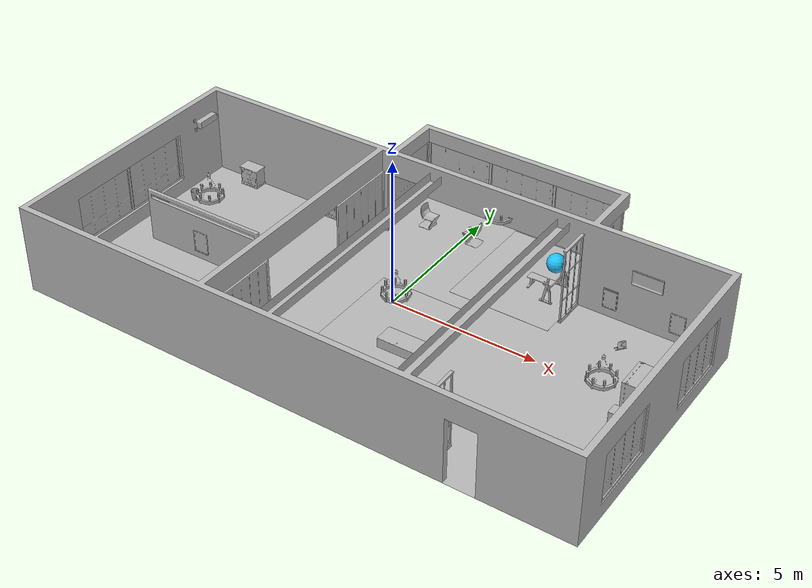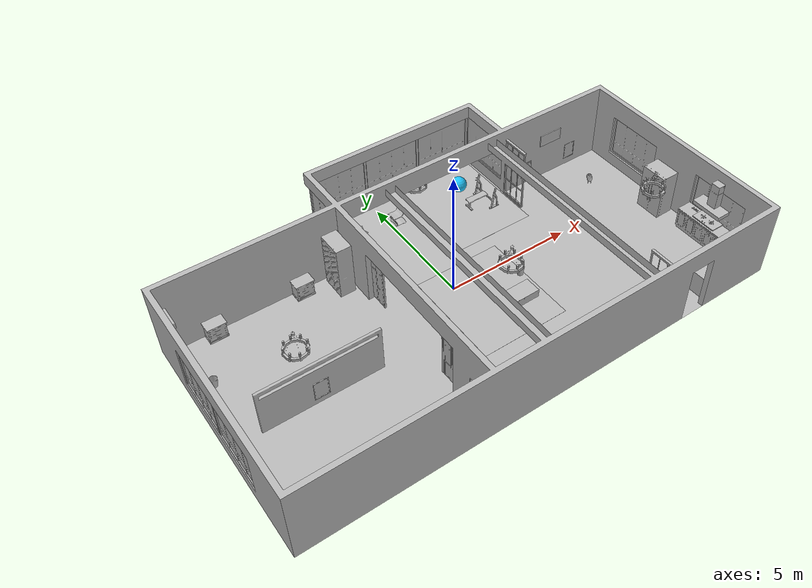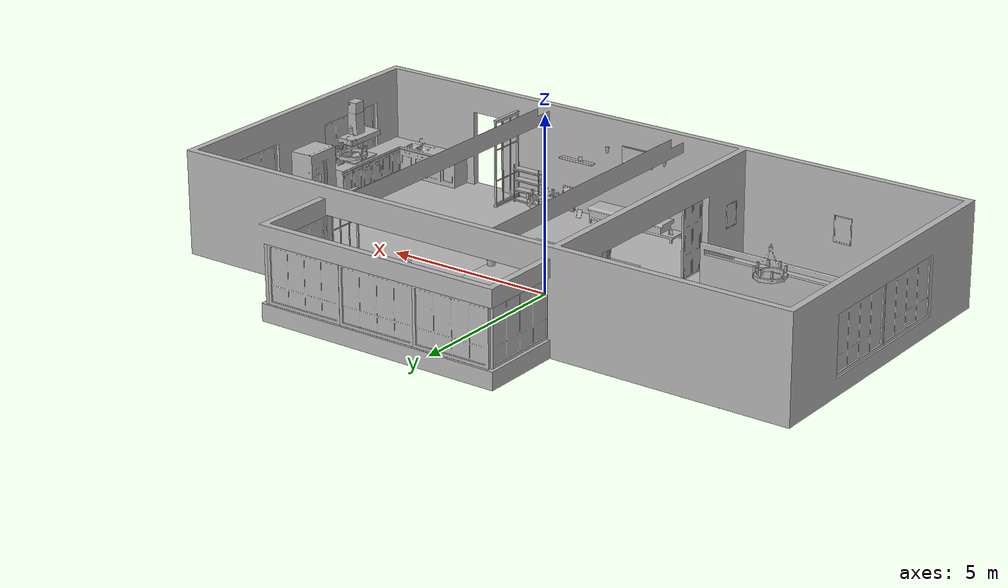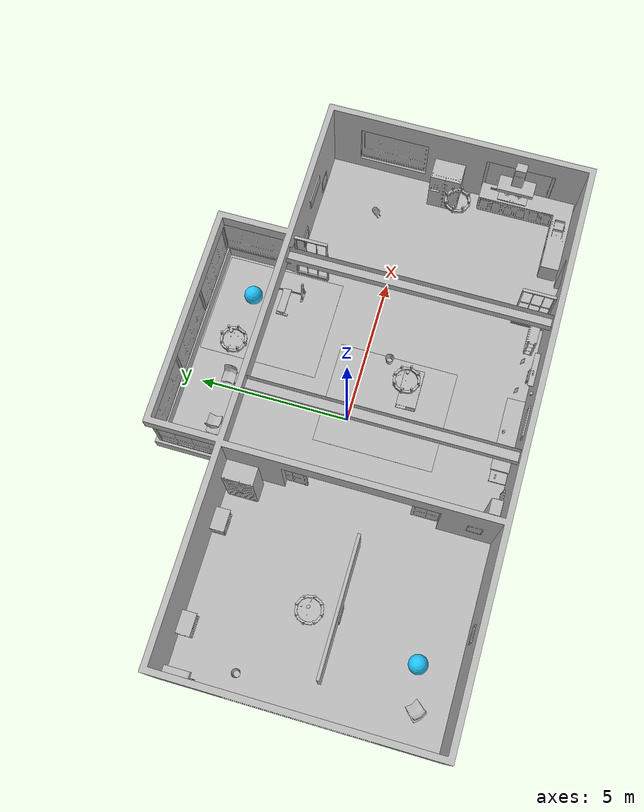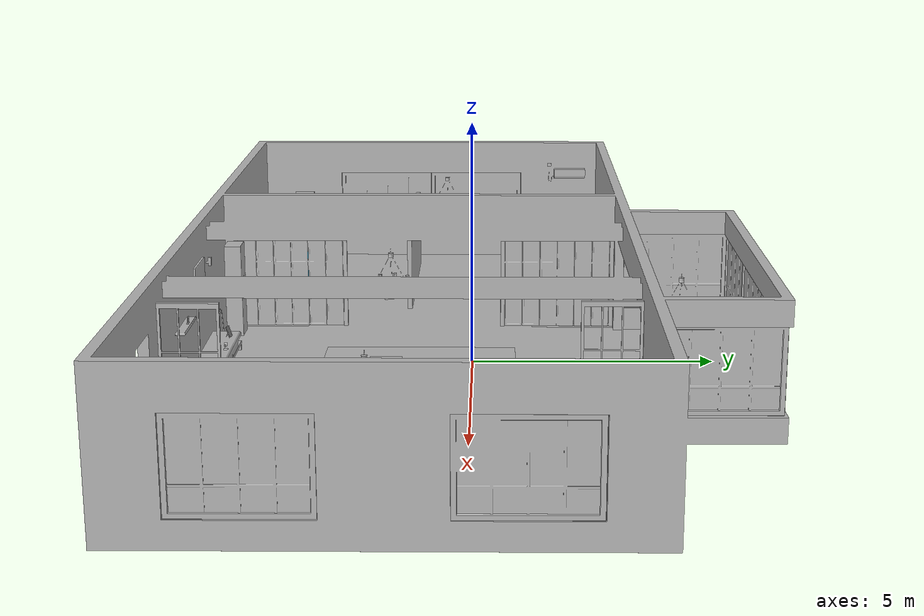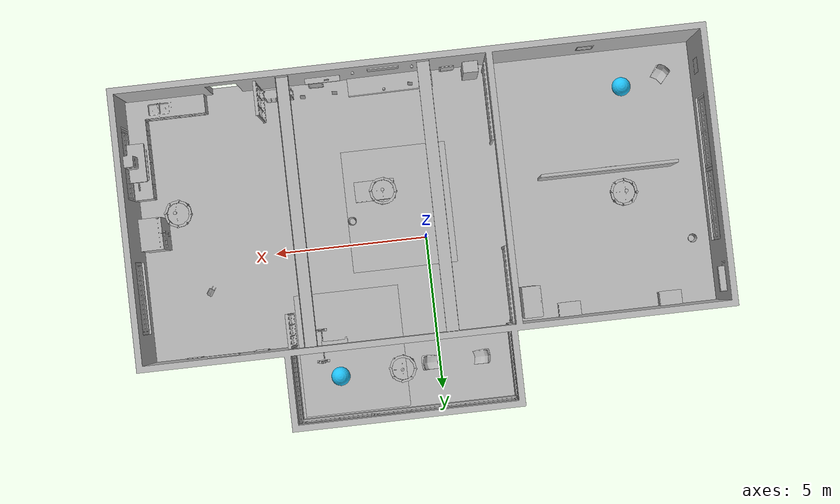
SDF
<sdf version="1.6">
 <world name="default">
  <plugin filename="gz-sim-physics-system" name="gz::sim::systems::Physics"/>
  <plugin filename="gz-sim-user-commands-system" name="gz::sim::systems::UserCommands"/>
  <plugin filename="gz-sim-scene-broadcaster-system" name="gz::sim::systems::SceneBroadcaster"/>
  <plugin filename="gz-sim-sensors-system" name="gz::sim::systems::Sensors">
   <render_engine>ogre2</render_engine>
  </plugin>
  <gravity>0 0 -9.8</gravity>
  <magnetic_field>6e-06 2.3e-05 -4.2e-05</magnetic_field>
  <atmosphere type="adiabatic"/>
  <physics name="default_physics" default="0" type="ode">
   <max_step_size>0.001</max_step_size>
   <real_time_factor>1</real_time_factor>
   <real_time_update_rate>1000</real_time_update_rate>
  </physics>
  <scene>
   <ambient>0.4 0.4 0.4 1</ambient>
   <background>0.7 0.7 0.7 1</background>
   <shadows>false</shadows>
   <grid>false</grid>
   <origin_visual>false</origin_visual>
  </scene>
  <spherical_coordinates>
   <surface_model>EARTH_WGS84</surface_model>
   <latitude_deg>0</latitude_deg>
   <longitude_deg>0</longitude_deg>
   <elevation>0</elevation>
   <heading_deg>0</heading_deg>
  </spherical_coordinates>
  <model name="AirconditionerA_01_001">
   <static>true</static>
   <include><uri>model://aws_robomaker_residential_AirconditionerA_01</uri></include>
   <pose>-9.199410 2.411230 2.084544 0 -0 0</pose>
  </model>
  <model name="AirconditionerB_01_001">
   <static>true</static>
   <include><uri>model://aws_robomaker_residential_AirconditionerB_01</uri></include>
   <pose>-2.004656 -5.226610 0.003485 0 -0 0</pose>
  </model>
  <model name="Ball_01_001">
   <static>true</static>
   <include><uri>model://aws_robomaker_residential_Ball_01</uri></include>
   <pose>3.295503 4.225674 0.318684 0 -0 0</pose>
  </model>
  <model name="Ball_01_003">
   <static>true</static>
   <include><uri>model://aws_robomaker_residential_Ball_01</uri></include>
   <pose>-6.945503 -4.22174 0.318684 0 -0 0</pose>
  </model>
  <model name="NightStand_01_001">
   <static>true</static>
   <include><uri>model://aws_robomaker_residential_NightStand_01</uri></include>
   <pose>-7.725510 2.860420 0.005258 -0.000002 0 0</pose>
  </model>
  <model name="NightStand_01_002">
   <static>true</static>
   <include><uri>model://aws_robomaker_residential_NightStand_01</uri></include>
   <pose>-4.407341 2.860420 0.005256 0 0.000002 0</pose>
  </model>
  <model name="Board_01_001">
   <static>true</static>
   <include><uri>model://aws_robomaker_residential_Board_01</uri></include>
   <pose>2.779073 -5.392703 1.538173 0 -0 0</pose>
  </model>
  <model name="ChairD_01_001">
   <static>true</static>
   <include><uri>model://aws_robomaker_residential_ChairD_01</uri></include>
   <pose>-1.380775 4.104456 0 0 -0 0</pose>
  </model>
  <model name="ChairD_01_002">
   <static>true</static>
   <include><uri>model://aws_robomaker_residential_ChairD_01</uri></include>
   <pose>0.325214 4.104456 0 0 -0 -3.138741</pose>
  </model>
  <model name="ChairD_01_003">
   <static>true</static>
   <include><uri>model://aws_robomaker_residential_ChairD_01</uri></include>
   <pose>-8.270775 -4.504456 0 0 -0 0.869673</pose>
  </model>
  <model name="Chandelier_01_001">
   <static>true</static>
   <include><uri>model://aws_robomaker_residential_Chandelier_01</uri></include>
   <pose>1.221061 4.155740 1.295000 0 -0 0</pose>
  </model>
  <model name="Chandelier_01_002">
   <static>true</static>
   <include><uri>model://aws_robomaker_residential_Chandelier_01</uri></include>
   <pose>-6.451061 -0.692040 1.810000 0 -0 0</pose>
  </model>
  <model name="Chandelier_01_003">
   <static>true</static>
   <include><uri>model://aws_robomaker_residential_Chandelier_01</uri></include>
   <pose>7.824061 -1.59 1.7510000 0 -0 0</pose>
  </model>
  <model name="Chandelier_01_004">
   <static>true</static>
   <include><uri>model://aws_robomaker_residential_Chandelier_01</uri></include>
   <pose>1.221061 -1.592040 1.7873000 0 -0 0</pose>
  </model>
  <model name="Carpet_01_001">
   <static>true</static>
   <include><uri>model://aws_robomaker_residential_Carpet_01</uri></include>
   <pose>0.785050 -1.106647 0.001106 0 -0 0</pose>
  </model>
  <model name="Carpet_01_002">
   <static>true</static>
   <include><uri>model://aws_robomaker_residential_Carpet_01</uri></include>
   <pose>2.854050 3.45 0.000585 0 -0 0</pose>
  </model>
  <model name="SecurityCamera_01_001">
   <static>true</static>
   <include><uri>model://aws_robomaker_residential_SecurityCamera_01</uri></include>
   <pose>0.842134 -4.996294 0.495067 0 -0 -2.841039</pose>
  </model>
  <model name="CoffeeTable_01_001">
   <static>true</static>
   <include><uri>model://aws_robomaker_residential_CoffeeTable_01</uri></include>
   <pose>1.512301 -1.733438 0.041983 0.000000 0.000000 0.01000</pose>
  </model>
  <model name="CookingBench_01_001">
   <include><uri>model://aws_robomaker_residential_CookingBench_01</uri></include>
   <pose>9.038383 -3.351140 0.903610 0 -0 3.137133</pose>
   <static>true</static>
  </model>
  <model name="FitnessEquipment_01_001">
   <static>true</static>
   <include><uri>model://aws_robomaker_residential_FitnessEquipment_01</uri></include>
   <pose>3.484720 3.169104 0.003168 0 -0 0</pose>
  </model>
  <model name="FoldingDoor_01_001">
   <static>true</static>
   <include><uri>model://aws_robomaker_residential_FoldingDoor_01</uri></include>
   <pose>-2.461096 1.844219 0.041881 0 -0 0</pose>
  </model>
  <model name="FoldingDoor_01_002">
   <static>true</static>
   <include><uri>model://aws_robomaker_residential_FoldingDoor_01</uri></include>
   <pose>-2.461096 -4.053320 0.041881 0 -0 0</pose>
  </model>
  <model name="HouseWallB_01_001">
   <static>true</static>
   <include><uri>model://aws_robomaker_residential_HouseWallB_01</uri></include>
  </model>
  <model name="FloorB_01_001">
   <static>true</static>
   <include><uri>model://aws_robomaker_residential_FloorB_01</uri></include>
  </model>
  <model name="FoldingDoor_02_001">
   <static>true</static>
   <include><uri>model://aws_robomaker_residential_FoldingDoor_02</uri></include>
   <pose>4.674231 2.46451 0 0 -0 3.14159</pose>
  </model>
  <model name="FoldingDoor_02_002">
   <static>true</static>
   <include><uri>model://aws_robomaker_residential_FoldingDoor_02</uri></include>
   <pose>4.8912 -4.84968 0 0 -0 0</pose>
  </model>
  <model name="KitchenCabinet_01_001">
   <static>true</static>
   <include><uri>model://aws_robomaker_residential_KitchenCabinet_01</uri></include>
   <pose>8.002009 -3.836509 0.012068 0 -0 -3.140001</pose>
  </model>
  <model name="LightC_01_001">
   <static>true</static>
   <include><uri>model://aws_robomaker_residential_LightC_01</uri></include>
   <pose>1.769567 -5.4443710 2.000000 0 -0 0</pose>
  </model>
  <model name="LightC_01_002">
   <static>true</static>
   <include><uri>model://aws_robomaker_residential_LightC_01</uri></include>
   <pose>-0.138245 -5.4443710 2.000000 0 -0 0</pose>
  </model>
  <model name="PortraitA_01">
   <static>true</static>
   <include><uri>model://aws_robomaker_residential_PortraitA_01</uri></include>
   <pose>-2.712360 -4.817539 1.00000 0 -0 1.566796</pose>
  </model>
  <model name="PortraitB_01">
   <static>true</static>
   <include><uri>model://aws_robomaker_residential_PortraitB_01</uri></include>
   <pose>-1.279683 -5.429630 0.0 -0.076901 0 -3.116718</pose>
  </model>
  <model name="PortraitB_02">
   <static>true</static>
   <include><uri>model://aws_robomaker_residential_PortraitB_02</uri></include>
   <pose>5.737017 3.080310 0.300000 0 -0 0</pose>
  </model>
  <model name="PortraitB_03">
   <static>true</static>
   <include><uri>model://aws_robomaker_residential_PortraitB_03</uri></include>
   <pose>3.071380 -5.349366 0.005494 -0.168428 0.0 3.104232</pose>
  </model>
  <model name="PortraitA_02">
   <static>true</static>
   <include><uri>model://aws_robomaker_residential_PortraitA_02</uri></include>
   <pose>7.937017 3.080310 0.300000 0 -0 3.14</pose>
  </model>
  <model name="PortraitC_01">
   <static>true</static>
   <include><uri>model://aws_robomaker_residential_PortraitC_01</uri></include>
   <pose>-9.294904 -4.526084 1.000000 0 -0 1.554734</pose>
  </model>
  <model name="PortraitD_01">
   <static>true</static>
   <include><uri>model://aws_robomaker_residential_PortraitD_01</uri></include>
   <pose>0.789763 -5.478725 1.800000 0 -0 3.138531</pose>
  </model>
  <model name="PortraitD_02">
   <static>true</static>
   <include><uri>model://aws_robomaker_residential_PortraitD_02</uri></include>
   <pose>6.870181 3.080310 1.488439 0 -0 0</pose>
  </model>
  <model name="PortraitE_01">
   <static>true</static>
   <include><uri>model://aws_robomaker_residential_PortraitE_01</uri></include>
   <pose>-5.773094 -5.492466 1.000000 0 -0 3.132627</pose>
  </model>
  <model name="PortraitE_02">
   <static>true</static>
   <include><uri>model://aws_robomaker_residential_PortraitE_02</uri></include>
   <pose>-6.193025 -1.590208 0.3 0 -0 0.004290</pose>
  </model>
  <model name="DeskPortraitA_01">
   <static>true</static>
   <include><uri>model://aws_robomaker_residential_DeskPortraitA_01</uri></include>
   <pose>-0.036864 -5.110156 0.498660 0 -0 2.927784</pose>
  </model>
  <model name="DeskPortraitA_02">
   <static>true</static>
   <include><uri>model://aws_robomaker_residential_DeskPortraitA_02</uri></include>
   <pose>2.046082 -1.892926 0.0703880 -0.018328 -0.000441 1.576216</pose>
  </model>
  <model name="DeskPortraitD_01">
   <static>true</static>
   <include><uri>model://aws_robomaker_residential_DeskPortraitD_01</uri></include>
   <pose>2.645560 -5.376225 1.573738 0 -0 -3.112826</pose>
  </model>
  <model name="DeskPortraitD_02">
   <static>true</static>
   <include><uri>model://aws_robomaker_residential_DeskPortraitD_02</uri></include>
   <pose>-0.589211 -5.109890 0.192145 -0.000015 -0.000174 -3.112544</pose>
  </model>
  <model name="DeskPortraitD_03">
   <static>true</static>
   <include><uri>model://aws_robomaker_residential_DeskPortraitD_03</uri></include>
   <pose>1.826729 -1.464881 0.126208 0.000010 0.000006 -3.114380</pose>
  </model>
  <model name="DeskPortraitD_04">
   <static>true</static>
   <include><uri>model://aws_robomaker_residential_DeskPortraitD_04</uri></include>
   <pose>4.302132 -5.176568 0.202496 0.007118 -0.000001 3.046683</pose>
  </model>
  <model name="DeskPortraitB_01">
   <static>true</static>
   <include><uri>model://aws_robomaker_residential_DeskPortraitB_01</uri></include>
   <pose>3.547376 -5.083898 -0.012660 -0.336622 -0.000001 3.046741</pose>
  </model>
  <model name="DeskPortraitB_02">
   <static>true</static>
   <include><uri>model://aws_robomaker_residential_DeskPortraitB_02</uri></include>
   <pose>2.486270 -5.102525 -0.012660 -0.336621 0.000000 3.046798</pose>
  </model>
  <model name="Rangehood_01_001">
   <static>true</static>
   <include><uri>model://aws_robomaker_residential_Rangehood_01</uri></include>
   <pose>9.019794 -3.369940 1.507605 0 -0 0</pose>
  </model>
  <model name="Refrigerator_01_001">
   <static>true</static>
   <include><uri>model://aws_robomaker_residential_Refrigerator_01</uri></include>
   <pose>8.702731 -1.032031 0 0 -0 -1.563499</pose>
  </model>
  <model name="SeasoningBox_01_001">
   <static>true</static>
   <include><uri>model://aws_robomaker_residential_SeasoningBox_01</uri></include>
   <pose>9.107968 -2.651726 0.902458 -0.000006 0.000034 0.001290</pose>
  </model>
  <model name="ShoeRack_01_001">
   <static>true</static>
   <include><uri>model://aws_robomaker_residential_ShoeRack_01</uri></include>
   <pose>4.297978 -5.173566 0 0 -0 0</pose>
  </model>
  <model name="Tableware_01_001">
   <static>true</static>
   <include><uri>model://aws_robomaker_residential_Tableware_01</uri></include>
   <pose>7.15317 0.982767 0.817812 -0.001238 -0.000976 1.02476</pose>
  </model>
  <model name="Trash_01_001">
   <static>true</static>
   <include><uri>model://aws_robomaker_residential_Trash_01</uri></include>
   <pose>2.360151 -0.796238 0.011 0 -0 0</pose>
  </model>
  <model name="Trash_01_002">
   <static>true</static>
   <include><uri>model://aws_robomaker_residential_Trash_01</uri></include>
   <pose>-8.704151 1.00058 0.011 0 -0 0</pose>
  </model>
  <model name="TVCabinet_01_001">
   <static>true</static>
   <include><uri>model://aws_robomaker_residential_TVCabinet_01</uri></include>
   <pose>0.629509 -5.183576 -0.017049 0 -0 1.5792</pose>
  </model>
  <model name="RoomWall_01_001">
   <static>true</static>
   <include><uri>model://aws_robomaker_residential_RoomWall_01</uri></include>
   <pose>-6.097550 -1.496180 0.028124 0 -0 0</pose>
  </model>
  <model name="Wardrobe_01_001">
   <static>true</static>
   <include><uri>model://aws_robomaker_residential_Wardrobe_01</uri></include>
   <pose>-3.146710 2.476204 0.000704 0 -0 -1.569673</pose>
  </model>
  <model name="RoomWindow_01_001">
   <static>true</static>
   <include><uri>model://aws_robomaker_residential_RoomWindow_01</uri></include>
   <pose>-9.418600 -0.026285 0.502739 0 -0 0</pose>
  </model>
  <model name="RoomWindow_01_002">
   <static>true</static>
   <include><uri>model://aws_robomaker_residential_RoomWindow_01</uri></include>
   <pose>-9.418600 -2.374090 0.502739 0 -0 0</pose>
  </model>
  <model name="RoomWindow_01_003">
   <static>true</static>
   <include><uri>model://aws_robomaker_residential_RoomWindow_01</uri></include>
   <pose>9.422616 -3.373981 0.502739 0 -0 -3.136099</pose>
  </model>
  <model name="RoomWindow_01_004">
   <static>true</static>
   <include><uri>model://aws_robomaker_residential_RoomWindow_01</uri></include>
   <pose>9.422558 0.968520 0.496581 0 -0 -3.136099</pose>
  </model>
  <model name="RoomWindow_01_005">
   <static>true</static>
   <include><uri>model://aws_robomaker_residential_RoomWindow_01</uri></include>
   <pose>4.722317 4.470281 0.502739 0 -0 -3.136099</pose>
  </model>
  <model name="RoomWindow_01_006">
   <static>true</static>
   <include><uri>model://aws_robomaker_residential_RoomWindow_01</uri></include>
   <pose>3.488520 5.600688 0.502739 0 -0 -1.566274</pose>
  </model>
  <model name="RoomWindow_01_007">
   <static>true</static>
   <include><uri>model://aws_robomaker_residential_RoomWindow_01</uri></include>
   <pose>1.140949 5.600688 0.502739 0 -0 -1.566274</pose>
  </model>
  <model name="RoomWindow_01_008">
   <static>true</static>
   <include><uri>model://aws_robomaker_residential_RoomWindow_01</uri></include>
   <pose>-1.199340 5.600688 0.502739 0 -0 -1.566274</pose>
  </model>
  <model name="RoomWindow_01_009">
   <static>true</static>
   <include><uri>model://aws_robomaker_residential_RoomWindow_01</uri></include>
   <pose>-2.396624 4.387607 0.502739 0 -0 0</pose>
  </model>
  <light name="LivingRoom_CeilingLight_0" type="point">
   <pose>1.194296 4.155759 2.2 0 -0 0</pose>
   <diffuse>0.5 0.5 0.5 1</diffuse>
   <specular>0.1 0.1 0.1 1</specular>
   <attenuation>
    <range>20</range>
    <constant>0.32</constant>
    <linear>0.01</linear>
    <quadratic>0.03</quadratic>
   </attenuation>
   <cast_shadows>0</cast_shadows>
   <direction>0 0 -1</direction>
  </light>
  <light name="LivingRoom_CeilingLight_1" type="point">
   <pose>1.194296 -1.589959 2.2 0 -0 0</pose>
   <diffuse>0.5 0.5 0.5 1</diffuse>
   <specular>0.1 0.1 0.1 1</specular>
   <attenuation>
    <range>20</range>
    <constant>0.05</constant>
    <linear>0.01</linear>
    <quadratic>0.09</quadratic>
   </attenuation>
   <cast_shadows>0</cast_shadows>
   <direction>0 0 -1</direction>
  </light>
  <light name="LivingRoom_WallLight_0" type="point">
   <pose>1.76956 -5.444370 2.2 0 -0 0</pose>
   <diffuse>0.24 0.24 0.24 1</diffuse>
   <specular>0.1 0.1 0.1 1</specular>
   <attenuation>
    <range>20</range>
    <constant>0.12</constant>
    <linear>0.00</linear>
    <quadratic>0.03</quadratic>
   </attenuation>
   <direction>0 0 -1</direction>
  </light>
  <light name="LivingRoom_WallLight_1" type="point">
   <pose>-0.13826 -5.444370 2.2 0 -0 0</pose>
   <diffuse>0.24 0.24 0.24 1</diffuse>
   <specular>0.1 0.1 0.1 1</specular>
   <attenuation>
    <range>20</range>
    <constant>0.12</constant>
    <linear>0.00</linear>
    <quadratic>0.03</quadratic>
   </attenuation>
   <direction>0 0 -1</direction>
  </light>
  <light name="TV_Light_0" type="point">
   <pose>0.8269 -4.939577 1.1 0 -0 0</pose>
   <diffuse>0.31372 0.31372 0.34901 1</diffuse>
   <specular>0.1 0.1 0.1 1</specular>
   <attenuation>
    <range>3</range>
    <constant>0.10</constant>
    <linear>0.04</linear>
    <quadratic>0.50</quadratic>
   </attenuation>
   <direction>0 0 -1</direction>
  </light>
  <light name="BedRoom_Portrait_Light_0" type="spot">
   <pose>-6.190379 -1.829697 1.5587 0.3 -0 0.0</pose>
   <diffuse>0.5 0.5 0.5 1</diffuse>
   <specular>0.1 0.1 0.1 1</specular>
   <attenuation>
    <range>20</range>
    <constant>0.50</constant>
    <linear>0.01</linear>
    <quadratic>0.00</quadratic>
   </attenuation>
   <spot><inner_angle>0.6</inner_angle><outer_angle>1.0</outer_angle><falloff>1.0</falloff></spot>
   <direction>0 0 -1</direction>
  </light>
  <light name="BedRoom_CeilingLight_0" type="point">
   <pose>-6.451061 -0.692040 2.000000 0 -0 0</pose>
   <diffuse>0.5 0.5 0.5 1</diffuse>
   <specular>0.1 0.1 0.1 1</specular>
   <attenuation>
    <range>20</range>
    <constant>0.32</constant>
    <linear>0.01</linear>
    <quadratic>0.03</quadratic>
   </attenuation>
   <cast_shadows>0</cast_shadows>
   <direction>0 0 -1</direction>
  </light>
  <light name="Kitchen_CeilingLight_0" type="point">
   <pose>7.8582 -1.5905 2.280000 0 -0 0</pose>
   <diffuse>0.5 0.5 0.5 1</diffuse>
   <specular>0.1 0.1 0.1 1</specular>
   <attenuation>
    <range>20</range>
    <constant>0.3</constant>
    <linear>0.01</linear>
    <quadratic>0.01</quadratic>
   </attenuation>
   <cast_shadows>0</cast_shadows>
   <direction>0 0 -1</direction>
  </light>
 </world>
</sdf>

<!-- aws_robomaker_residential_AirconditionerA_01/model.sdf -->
<sdf version="1.6">
  <model name="aws_robomaker_residential_AirconditionerA_01">
    <link name="AirconditionerA_01">
      <inertial>
        <mass>1</mass>
	<inertia>
	    <ixx>  8.0943111097e-02 </ixx>
	    <ixy> -8.1265470074e-06 </ixy>
	    <ixz>  3.8829570571e-03 </ixz>
	    <iyy>  7.7648100944e-02 </iyy>
	    <iyz>  5.1340621216e-05 </iyz>
	    <izz>  1.1188592910e-02 </izz>
	  </inertia>
	</inertial>
      <collision name="collision">
        <geometry>
          <mesh>
            <uri>model://aws_robomaker_residential_AirconditionerA_01/meshes/aws_AirconditionerA_01_collision.DAE</uri>
            <scale>1 1 1</scale>
          </mesh>
        </geometry>
      </collision>
      <visual name="visual">
	    <geometry>
          <mesh>
            <uri>model://aws_robomaker_residential_AirconditionerA_01/meshes/aws_AirconditionerA_01_visual.DAE</uri>
          </mesh>
        </geometry>
      <meta> <layer> 1 </layer></meta>
</visual>
    </link>
	<static>1</static>
  </model>
</sdf>

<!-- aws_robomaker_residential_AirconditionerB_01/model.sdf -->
<sdf version="1.6">
  <model name="aws_robomaker_residential_AirconditionerB_01">
    <link name="AirconditionerB_01">
      <inertial>
        <mass>1</mass>
        <inertia>
            <ixx>  3.5606825555e-01 </ixx>
            <ixy> -4.7724185539e-11 </ixy>
            <ixz>  4.6632465087e-14 </ixz>
            <iyy>  3.5592090264e-02 </iyy>
            <iyz> -2.6310178830e-11 </iyz>
            <izz>  3.6376805669e-01 </izz>
        </inertia>
      </inertial>
      <collision name="collision">
        <geometry>
          <mesh>
            <uri>model://aws_robomaker_residential_AirconditionerB_01/meshes/aws_AirconditionerB_01_collision.DAE</uri>
            <scale>1 1 1</scale>
          </mesh>
        </geometry>
      </collision>
      <visual name="visual">
	    <geometry>
          <mesh>
            <uri>model://aws_robomaker_residential_AirconditionerB_01/meshes/aws_AirconditionerB_01_visual.DAE</uri>
          </mesh>
        </geometry>
      <meta> <layer> 1 </layer></meta>
</visual>
    </link>
  </model>
</sdf>

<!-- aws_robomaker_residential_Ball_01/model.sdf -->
<sdf version="1.6">
  <model name="aws_robomaker_residential_Ball_01">
    <link name="Ball_01">
      <inertial>
        <mass>0.12</mass>
	<inertia>
	    <ixx>  3.8749023340e-02 </ixx>
	    <ixy> -1.0450629836e-09 </ixy>
	    <ixz>  4.9179161356e-09 </ixz>
	    <iyy>  3.8433714890e-02 </iyy>
	    <iyz>  5.9071629616e-11 </iyz>
	    <izz>  3.8749023340e-02 </izz>
	  </inertia>
	</inertial>
      <collision name="collision">

        <geometry>
          <sphere>
            <radius>0.31 </radius>
          </sphere>

        </geometry>

        <surface>
          <friction>
            <ode>
              <mu>0.85</mu>
              <mu2>0.85</mu2>
            </ode>
          </friction>

        <!-- Add some bounciness to the ball -->
          <contact>
            <ode>
              <kd>8500</kd>
              <max_vel>5.1</max_vel>
            </ode>
          </contact>
        </surface>

      </collision>
      <visual name="visual">
	    <geometry>
          <sphere>
            <radius>0.31 </radius>
          </sphere>
      </geometry>
          <material>
            <diffuse>0.12 0.76 0.97 1</diffuse>
            <ambient>0.03 0.21 0.27 1</ambient>
          </material>
      <meta> <layer> 1 </layer></meta>
</visual>
    </link>
  </model>
</sdf>

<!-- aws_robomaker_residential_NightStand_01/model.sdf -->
<sdf version="1.6">
  <model name="aws_robomaker_residential_NightStand_01">
    <link name="link">
      <inertial>
        <mass>13.6</mass>
	<inertia>
	    <ixx>  5.9068121342e-02 </ixx>
	    <ixy> -0.0000000000e+00 </ixy>
	    <ixz>  0.0000000000e+00 </ixz>
	    <iyy>  6.4866772161e-02 </iyy>
	    <iyz>  0.0000000000e+00 </iyz>
	    <izz>  8.5677794724e-02 </izz>
	  </inertia>
	</inertial>
      <collision name="collision">
        <geometry>
          <mesh>
            <uri>model://aws_robomaker_residential_NightStand_01/meshes/aws_NightStand_01_collision.DAE</uri>
            <scale>1 1 1</scale>
          </mesh>
        </geometry>
      </collision>
      <visual name="visual">
	    <geometry>
          <mesh>
            <uri>model://aws_robomaker_residential_NightStand_01/meshes/aws_NightStand_01_visual.DAE</uri>
          </mesh>
        </geometry>
      <meta> <layer> 1 </layer></meta>
</visual>
    </link>
    <static>1</static>
  </model>
</sdf>

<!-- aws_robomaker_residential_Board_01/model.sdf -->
<sdf version="1.6">
  <model name="aws_robomaker_residential_Board_01">
    <link name="link">
      <inertial>
        <mass>1</mass>
        <inertia>
            <ixx>  3.5606825555e-01 </ixx>
            <ixy> -4.7724185539e-11 </ixy>
            <ixz>  4.6632465087e-14 </ixz>
            <iyy>  3.5592090264e-02 </iyy>
            <iyz> -2.6310178830e-11 </iyz>
            <izz>  3.6376805669e-01 </izz>
        </inertia>
      </inertial>
      <collision name="collision">
        <geometry>
          <mesh>
            <uri>model://aws_robomaker_residential_Board_01/meshes/aws_Board_01_collision.DAE</uri>
            <scale>1 1 1</scale>
          </mesh>
        </geometry>
      </collision>
      <visual name="visual">
	    <geometry>
          <mesh>
            <uri>model://aws_robomaker_residential_Board_01/meshes/aws_Board_01_visual.DAE</uri>
          </mesh>
        </geometry>
      <meta> <layer> 2 </layer></meta>
</visual>
    </link>

    <static>1</static>
  </model>
</sdf>

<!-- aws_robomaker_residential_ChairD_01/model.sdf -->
<sdf version="1.6">
  <model name="aws_robomaker_residential_ChairD_01">
    <link name="link">

      <inertial>
      <mass>8.5</mass>
	<inertia>
	    <ixx>  5.5200427517e-02 </ixx>
	    <ixy>  1.2896722661e-02 </ixy>
	    <ixz>  1.5893767493e-04 </ixz>
	    <iyy>  4.0396087891e-02 </iyy>
	    <iyz> -2.8293607821e-04 </iyz>
	    <izz>  6.5806204881e-02 </izz>
	  </inertia>
	</inertial>

      <collision name="collision">

        <geometry>
          <mesh>
            <uri>model://aws_robomaker_residential_ChairD_01/meshes/aws_ChairD_01_collision.DAE</uri>
            <scale>1 1 1</scale>
          </mesh>
        </geometry>

      </collision>
      <visual name="visual">
	    <geometry>
          <mesh>
            <uri>model://aws_robomaker_residential_ChairD_01/meshes/aws_ChairD_01_visual.DAE</uri>
          </mesh>
        </geometry>
      <meta> <layer> 1 </layer></meta>
</visual>
    </link>
  </model>
</sdf>

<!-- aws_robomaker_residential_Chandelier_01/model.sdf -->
<sdf version="1.6">
  <model name="aws_robomaker_residential_Chandelier_01">
    <link name="link">
      <inertial>
        <mass>1</mass>
	<inertia>
	    <ixx>  9.8314889873e-02 </ixx>
	    <ixy>  8.1564130546e-05 </ixy>
	    <ixz> -2.2898136825e-09 </ixz>
	    <iyy>  1.1882498465e-01 </iyy>
	    <iyz> -1.1171926154e-10 </iyz>
	    <izz>  9.7043315192e-02 </izz>
	  </inertia>
	</inertial>
      <collision name="collision">
        <geometry>
          <mesh>
            <uri>model://aws_robomaker_residential_Chandelier_01/meshes/aws_Chandelier_01_collision.DAE</uri>
            <scale>1 1 1</scale>
          </mesh>
        </geometry>
      </collision>
      <visual name="visual">
	    <geometry>
          <mesh>
            <uri>model://aws_robomaker_residential_Chandelier_01/meshes/aws_Chandelier_01_visual.DAE</uri>
          </mesh>
        </geometry>
      <meta> <layer> 2 </layer></meta>
</visual>
    </link>
	<static>1</static>
  </model>
</sdf>

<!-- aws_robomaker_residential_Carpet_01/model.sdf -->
<sdf version="1.6">
  <model name="aws_robomaker_residential_Carpet_01">
    <link name="link">
      <inertial>
        <mass>8.1</mass>
	<inertia>
	    <ixx>  1.3412920773e+00 </ixx>
	    <ixy> -0.0000000000e+00 </ixy>
	    <ixz>  0.0000000000e+00 </ixz>
	    <iyy>  2.3413254318e+00 </iyy>
	    <iyz>  0.0000000000e+00 </iyz>
	    <izz>  1.0000339302e+00 </izz>
	  </inertia>
	</inertial>

      <collision name="collision">

        <geometry>
          <mesh>
            <uri>model://aws_robomaker_residential_Carpet_01/meshes/aws_Carpet_01_collision.DAE</uri>
            <scale>1 1 0.95</scale>
          </mesh>
        </geometry>

        <surface>
          <contact>
            <ode>
            </ode>
          </contact>
        </surface>

        <pose>0 0 -0.01 0 0 0 </pose>
      </collision>

      <visual name="visual">
	    <geometry>
          <mesh>
            <uri>model://aws_robomaker_residential_Carpet_01/meshes/aws_Carpet_01_visual.DAE</uri>
          </mesh>
        </geometry>
      <meta> <layer> 1 </layer></meta>
</visual>
    </link>

    <static>1</static>

  </model>
</sdf>

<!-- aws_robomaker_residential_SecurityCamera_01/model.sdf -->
<sdf version="1.6">
  <model name="aws_robomaker_residential_SecurityCamera_01">
    <link name="link">
      <inertial>
        <mass>1</mass>
        <inertia>
          <ixx>18.2222</ixx>
          <ixy>0</ixy>
          <ixz>0</ixz>
          <iyy>18.2222</iyy>
          <iyz>0</iyz>
          <izz>0.0018767</izz>
        </inertia>
      </inertial>
      <collision name="collision">
        <geometry>
          <mesh>
            <uri>model://aws_robomaker_residential_SecurityCamera_01/meshes/aws_SecurityCamera_01_collision.DAE</uri>
            <scale>1 1 1</scale>
          </mesh>
        </geometry>
      </collision>
      <visual name="visual">
	    <geometry>
          <mesh>
            <uri>model://aws_robomaker_residential_SecurityCamera_01/meshes/aws_SecurityCamera_01_visual.DAE</uri>
          </mesh>
        </geometry>
        <meta>
          <layer>2</layer>
        </meta>
      </visual>
    </link>
  </model>
</sdf>

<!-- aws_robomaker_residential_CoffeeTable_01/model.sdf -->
<sdf version="1.6">
  <model name="aws_robomaker_residential_CoffeeTable_01">
    <link name="link">
      <inertial>
        <mass>21.7</mass>

        <inertia>
          <ixx>0.8137499999999998</ixx>
          <ixy>0</ixy>
          <ixz>0</ixz>
          <iyy>2.76675</iyy>
          <iyz>0</iyz>
          <izz>3.254</izz>
        </inertia>

      </inertial>

      <collision name="collision">
        <geometry>
          <mesh>
            <uri>model://aws_robomaker_residential_CoffeeTable_01/meshes/aws_CoffeeTable_01_collision.DAE</uri>
            <scale>1 1 1</scale>
          </mesh>
        </geometry>

        <surface>
          <contact>
            <ode>
              <max_vel>0.01</max_vel>
            </ode>
          </contact>
         </surface>
      </collision>

      <visual name="visual">
	    <geometry>
          <mesh>
            <uri>model://aws_robomaker_residential_CoffeeTable_01/meshes/aws_CoffeeTable_01_visual.DAE</uri>
          </mesh>
        </geometry>
      <meta> <layer> 1 </layer></meta>
</visual>
    </link>
    <static>1</static>
  </model>
</sdf>

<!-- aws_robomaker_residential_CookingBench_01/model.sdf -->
<sdf version="1.6">
  <model name="aws_robomaker_residential_CookingBench_01">
    <link name="link">
      <inertial>
        <mass>1</mass>
	<inertia>
	    <ixx>  8.4704931274e-02 </ixx>
	    <ixy> -3.3582970635e-14 </ixy>
	    <ixz> -1.8657205909e-15 </ixz>
	    <iyy>  1.0870613560e-01 </iyy>
	    <iyz> -8.9711047690e-09 </iyz>
	    <izz>  2.5599100723e-02 </izz>
	  </inertia>
	</inertial>
      <collision name="collision">
        <geometry>
          <mesh>
            <uri>model://aws_robomaker_residential_CookingBench_01/meshes/aws_CookingBench_01_collision.DAE</uri>
            <scale>1 1 1</scale>
          </mesh>
        </geometry>
      </collision>
      <visual name="visual">
	    <geometry>
          <mesh>
            <uri>model://aws_robomaker_residential_CookingBench_01/meshes/aws_CookingBench_01_visual.DAE</uri>
          </mesh>
        </geometry>
      <meta> <layer> 1 </layer></meta>
</visual>
    </link>
  </model>
</sdf>

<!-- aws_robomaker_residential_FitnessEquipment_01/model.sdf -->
<sdf version="1.6">
  <model name="aws_robomaker_residential_FitnessEquipment_01">
    <link name="link">
      <inertial>
        <mass>80</mass>
	<inertia>
	    <ixx>  1.5231681051e-01 </ixx>
	    <ixy> -1.0236824255e-02 </ixy>
	    <ixz>  4.5347695138e-04 </ixz>
	    <iyy>  2.2216050074e-01 </iyy>
	    <iyz>  5.9325087530e-05 </iyz>
	    <izz>  1.4138500592e-01 </izz>
	  </inertia>
	</inertial>
      <collision name="collision">
        <geometry>
          <mesh>
            <uri>model://aws_robomaker_residential_FitnessEquipment_01/meshes/aws_FitnessEquipment_01_collision.DAE</uri>
            <scale>1 1 1</scale>
          </mesh>
        </geometry>
      </collision>
      <visual name="visual">
	    <geometry>
          <mesh>
            <uri>model://aws_robomaker_residential_FitnessEquipment_01/meshes/aws_FitnessEquipment_01_visual.DAE</uri>
          </mesh>
        </geometry>
      <meta> <layer> 1 </layer></meta>
</visual>
    </link>
  <static>1</static>
  </model>
</sdf>

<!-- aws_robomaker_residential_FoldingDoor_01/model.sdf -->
<sdf version="1.6">
  <model name="aws_robomaker_residential_FoldingDoor_01">
    <link name="link">
      <inertial>
        <mass>1</mass>
	<inertia>
	    <ixx>  9.3119001932e-01 </ixx>
	    <ixy>  2.9413508071e-11 </ixy>
	    <ixz>  2.9006137070e-14 </ixz>
	    <iyy>  5.2412406595e-01 </iyy>
	    <iyz>  2.8545710540e-11 </iyz>
	    <izz>  4.0867490543e-01 </izz>
	  </inertia>
	</inertial>
      <collision name="collision">
        <geometry>
          <mesh>
            <uri>model://aws_robomaker_residential_FoldingDoor_01/meshes/aws_FoldingDoor_01_collision.DAE</uri>
            <scale>1 1 1</scale>
          </mesh>
        </geometry>
      </collision>
      <visual name="visual">
	    <geometry>
          <mesh>
            <uri>model://aws_robomaker_residential_FoldingDoor_01/meshes/aws_FoldingDoor_01_visual.DAE</uri>
          </mesh>
        </geometry>
      <meta> <layer> 2 </layer></meta>
</visual>
    </link>
	<static>1</static>
  </model>
</sdf>

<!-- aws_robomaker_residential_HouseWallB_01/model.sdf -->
<sdf version="1.6">
  <model name="aws_robomaker_residential_HouseWallB_01">
    <link name="link">
      <inertial>
        <mass>1</mass>
        <inertia>
            <ixx>  3.5606825555e-01 </ixx>
            <ixy> -4.7724185539e-11 </ixy>
            <ixz>  4.6632465087e-14 </ixz>
            <iyy>  3.5592090264e-02 </iyy>
            <iyz> -2.6310178830e-11 </iyz>
            <izz>  3.6376805669e-01 </izz>
        </inertia>
      </inertial>
      <collision name="collision">
        <geometry>
          <mesh>
            <uri>model://aws_robomaker_residential_HouseWallB_01/meshes/aws_HouseWallB_01_collision.DAE</uri>
            <scale>1 1 1</scale>
          </mesh>
        </geometry>
      </collision>
      <visual name="visual">
	    <geometry>
          <mesh>
            <uri>model://aws_robomaker_residential_HouseWallB_01/meshes/aws_HouseWallB_01_visual.DAE</uri>
          </mesh>
        </geometry>
      <meta> <layer> 2 </layer></meta>
</visual>
    </link>
<static>1</static>
  </model>
</sdf>

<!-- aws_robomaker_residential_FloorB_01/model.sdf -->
<sdf version="1.6">
  <model name="aws_robomaker_residential_FloorB_01">
    <link name="link">
      <inertial>
        <mass>100</mass>
	<inertia>
	    <ixx>  8.9147242934e+00 </ixx>
	    <ixy> -2.1042172774e-11 </ixy>
	    <ixz>  5.6353464636e-01 </ixz>
	    <iyy>  3.6723713216e+01 </iyy>
	    <iyz> -5.7139224410e-10 </iyz>
	    <izz>  2.7809315968e+01 </izz>
	  </inertia>
	</inertial>

      <collision name="collision">
        <geometry>
          <mesh>
            <uri>model://aws_robomaker_residential_FloorB_01/meshes/aws_FloorB_01_collision.DAE</uri>
            <scale>1 1 0.9</scale>
          </mesh>
        </geometry>

        <surface>

        <!--
        src: https://www.engineeringtoolbox.com/friction-coefficients-d_778.html
        Wood (Clean & Dry Surfaces): 0.6
        -->
          <friction>
            <ode>
              <mu>0.6</mu>
              <mu2>0.6</mu2>
            </ode>
          </friction>

        </surface>

      </collision>

      <visual name="visual">
	    <geometry>
          <mesh>
            <uri>model://aws_robomaker_residential_FloorB_01/meshes/aws_FloorB_01_visual.DAE</uri>
          </mesh>
        </geometry>
      <meta> <layer> 1 </layer></meta>
</visual>
    </link>

	<static>1</static>
  </model>
</sdf>

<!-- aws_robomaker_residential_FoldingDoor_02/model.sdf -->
<sdf version="1.6">
  <model name="aws_robomaker_residential_FoldingDoor_02">
    <link name="link">
      <inertial>
        <mass>1</mass>
	<inertia>
	    <ixx>  6.7038465772e-01 </ixx>
	    <ixy>  1.3526701807e-11 </ixy>
	    <ixz>  1.5530775261e-13 </ixz>
	    <iyy>  1.0675443047e-01 </iyy>
	    <iyz>  2.9926273083e-09 </iyz>
	    <izz>  5.6555139368e-01 </izz>
	  </inertia>
	</inertial>
      <collision name="collision">
        <geometry>
          <mesh>
            <uri>model://aws_robomaker_residential_FoldingDoor_02/meshes/aws_FoldingDoor_02_collision.DAE</uri>
            <scale>1 1 1</scale>
          </mesh>
        </geometry>
      </collision>
      <visual name="visual">
	    <geometry>
          <mesh>
            <uri>model://aws_robomaker_residential_FoldingDoor_02/meshes/aws_FoldingDoor_02_visual.DAE</uri>
          </mesh>
        </geometry>
      <meta> <layer> 2 </layer></meta>
</visual>
    </link>
<static>1</static>
  </model>
</sdf>

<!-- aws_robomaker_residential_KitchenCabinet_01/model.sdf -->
<sdf version="1.6">
  <model name="aws_robomaker_residential_KitchenCabinet_01">
    <link name="link">
      <inertial>
        <mass>1</mass>
	<inertia>
	    <ixx>  1.0168440299e+00 </ixx>
	    <ixy> -7.6425744877e-04 </ixy>
	    <ixz>  3.9723161102e-01 </ixz>
	    <iyy>  1.4853953831e+00 </iyy>
	    <iyz>  1.1100048935e-03 </iyz>
	    <izz>  6.0507693907e-01 </izz>
	  </inertia>
	</inertial>
      <collision name="collision">
        <laser_retro>0</laser_retro>
        <max_contacts>10</max_contacts>
        <geometry>
          <mesh>
            <uri>model://aws_robomaker_residential_KitchenCabinet_01/meshes/aws_KitchenCabinet_01_collision.DAE</uri>
            <scale>1 1 1</scale>
          </mesh>
        </geometry>
      </collision>
      <visual name="visual">
	    <geometry>
          <mesh>
            <uri>model://aws_robomaker_residential_KitchenCabinet_01/meshes/aws_KitchenCabinet_01_visual.DAE</uri>
          </mesh>
        </geometry>
      <meta> <layer> 1 </layer></meta>
</visual>
    </link>

    <static>1</static>
  </model>
</sdf>

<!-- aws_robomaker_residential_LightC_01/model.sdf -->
<sdf version="1.6">
  <model name="aws_robomaker_residential_LightC_01">
    <link name="link">
      <inertial>
        <mass>1</mass>
	<inertia>
	    <ixx>  2.9810499065e-03 </ixx>
	    <ixy> -2.1245436995e-05 </ixy>
	    <ixz> -4.6128517701e-06 </ixz>
	    <iyy>  1.0491745309e-03 </iyy>
	    <iyz>  5.4737851285e-05 </iyz>
	    <izz>  2.9229620954e-03 </izz>
	  </inertia>
	</inertial>
      <collision name="collision">
        <geometry>
          <mesh>
            <uri>model://aws_robomaker_residential_LightC_01/meshes/aws_LightC_01_collision.DAE</uri>
            <scale>1 1 1</scale>
          </mesh>
        </geometry>
      </collision>
      <visual name="visual">
	    <geometry>
          <mesh>
            <uri>model://aws_robomaker_residential_LightC_01/meshes/aws_LightC_01_visual.DAE</uri>
          </mesh>
        </geometry>
      <meta> <layer> 2 </layer></meta>
</visual>
    </link>
	<static>1</static>
  </model>
</sdf>

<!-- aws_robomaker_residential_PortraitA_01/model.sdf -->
<sdf version="1.6">
  <model name="aws_robomaker_residential_PortraitA_01">
    <link name="link">
      <inertial>
        <mass>1	</mass>
	<inertia>
	    <ixx>  4.3388701859e-02 </ixx>
	    <ixy>  3.0630320763e-10 </ixy>
	    <ixz> -9.1092117801e-12 </ixz>
	    <iyy>  2.2485859760e-02 </iyy>
	    <iyz>  6.0319674257e-09 </iyz>
	    <izz>  6.5832494111e-02 </izz>
	  </inertia>
	</inertial>
      <collision name="collision">
        <geometry>
          <mesh>
            <uri>model://aws_robomaker_residential_PortraitA_01/meshes/aws_PortraitA_01_collision.DAE</uri>
            <scale>1 1 1</scale>
          </mesh>
        </geometry>
      </collision>
      <visual name="visual">
	    <geometry>
          <mesh>
            <uri>model://aws_robomaker_residential_PortraitA_01/meshes/aws_PortraitA_01_visual.DAE</uri>
          </mesh>
        </geometry>
      <meta> <layer> 2 </layer></meta>
</visual>
    </link>
	<static>1</static>
  </model>
</sdf>

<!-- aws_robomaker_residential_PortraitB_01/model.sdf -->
<sdf version="1.6">
  <model name="aws_robomaker_residential_PortraitB_01">
    <link name="link">
      <inertial>
        <mass>1</mass>
	<inertia>
	    <ixx>  4.0161427430e-02 </ixx>
	    <ixy>  1.4352328739e-06 </ixy>
	    <ixz> -3.6480670326e-07 </ixz>
	    <iyy>  2.0215045670e-02 </iyy>
	    <iyz> -4.3301252455e-07 </iyz>
	    <izz>  6.0277852191e-02 </izz>
	  </inertia>
	</inertial>
      <collision name="collision">
        <geometry>
          <mesh>
            <uri>model://aws_robomaker_residential_PortraitB_01/meshes/aws_PortraitB_01_collision.DAE</uri>
            <scale>1 1 1</scale>
          </mesh>
        </geometry>
      </collision>
      <visual name="visual">
	    <geometry>
          <mesh>
            <uri>model://aws_robomaker_residential_PortraitB_01/meshes/aws_PortraitB_01_visual.DAE</uri>
          </mesh>
        </geometry>
      <meta> <layer> 2 </layer></meta>
</visual>
    </link>
	<static>1</static>
  </model>
</sdf>

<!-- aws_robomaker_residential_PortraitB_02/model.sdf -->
<sdf version="1.6">
  <model name="aws_robomaker_residential_PortraitB_02">
    <link name="link">
      <inertial>
        <mass>1</mass>
	<inertia>
	    <ixx>  4.0161427430e-02 </ixx>
	    <ixy>  1.4352328739e-06 </ixy>
	    <ixz> -3.6480670326e-07 </ixz>
	    <iyy>  2.0215045670e-02 </iyy>
	    <iyz> -4.3301252455e-07 </iyz>
	    <izz>  6.0277852191e-02 </izz>
	  </inertia>
	</inertial>
      <collision name="collision">
        <geometry>
          <mesh>
            <uri>model://aws_robomaker_residential_PortraitB_02/meshes/aws_PortraitB_01_collision.DAE</uri>
            <scale>1 1 1</scale>
          </mesh>
        </geometry>
      </collision>
      <visual name="visual">
	    <geometry>
          <mesh>
            <uri>model://aws_robomaker_residential_PortraitB_02/meshes/aws_PortraitB_01_visual.DAE</uri>
          </mesh>
        </geometry>
      <meta> <layer> 2 </layer></meta>
</visual>
    </link>
	<static>1</static>
  </model>
</sdf>

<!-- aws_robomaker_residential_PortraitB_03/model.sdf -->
<sdf version="1.6">
  <model name="aws_robomaker_residential_PortraitB_03">
    <link name="link">
      <inertial>
        <mass>1</mass>
	<inertia>
	    <ixx>  4.0161427430e-02 </ixx>
	    <ixy>  1.4352328739e-06 </ixy>
	    <ixz> -3.6480670326e-07 </ixz>
	    <iyy>  2.0215045670e-02 </iyy>
	    <iyz> -4.3301252455e-07 </iyz>
	    <izz>  6.0277852191e-02 </izz>
	  </inertia>
	</inertial>
      <collision name="collision">
        <geometry>
          <mesh>
            <uri>model://aws_robomaker_residential_PortraitB_03/meshes/aws_PortraitB_01_collision.DAE</uri>
            <scale>1 1 1</scale>
          </mesh>
        </geometry>
      </collision>
      <visual name="visual">
	    <geometry>
          <mesh>
            <uri>model://aws_robomaker_residential_PortraitB_03/meshes/aws_PortraitB_01_visual.DAE</uri>
          </mesh>
        </geometry>
      <meta> <layer> 2 </layer></meta>
</visual>
    </link>
	<static>1</static>
  </model>
</sdf>

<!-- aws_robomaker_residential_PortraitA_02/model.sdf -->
<sdf version="1.6">
  <model name="aws_robomaker_residential_PortraitA_02">
    <link name="link">
      <inertial>
        <mass>1</mass>
	<inertia>
	    <ixx>  4.3388701859e-02 </ixx>
	    <ixy>  3.0630320763e-10 </ixy>
	    <ixz> -9.1092117801e-12 </ixz>
	    <iyy>  2.2485859760e-02 </iyy>
	    <iyz>  6.0319674257e-09 </iyz>
	    <izz>  6.5832494111e-02 </izz>
	  </inertia>
	</inertial>
      <collision name="collision">
        <geometry>
          <mesh>
            <uri>model://aws_robomaker_residential_PortraitA_02/meshes/aws_PortraitA_01_collision.DAE</uri>
            <scale>1 1 1</scale>
          </mesh>
        </geometry>
      </collision>
      <visual name="visual">
	    <geometry>
          <mesh>
            <uri>model://aws_robomaker_residential_PortraitA_02/meshes/aws_PortraitA_01_visual.DAE</uri>
          </mesh>
        </geometry>
      <meta> <layer> 2 </layer></meta>
</visual>
    </link>
	<static>1</static>
  </model>
</sdf>

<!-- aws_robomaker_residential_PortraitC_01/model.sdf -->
<sdf version="1.6">
  <model name="aws_robomaker_residential_PortraitC_01">
    <link name="link">
      <inertial>
        <mass>1</mass>
	<inertia>
	    <ixx>  4.1680920499e-02 </ixx>
	    <ixy>  8.8324870279e-09 </ixy>
	    <ixz> -2.4337601335e-09 </ixz>
	    <iyy>  2.1315698356e-02 </iyy>
	    <iyz>  9.3247699585e-09 </iyz>
	    <izz>  6.2960942901e-02 </izz>
	  </inertia>
	</inertial>
      <collision name="collision">
        <geometry>
          <mesh>
            <uri>model://aws_robomaker_residential_PortraitC_01/meshes/aws_PortraitC_01_collision.DAE</uri>
            <scale>1 1 1</scale>
          </mesh>
        </geometry>
      </collision>
      <visual name="visual">
	    <geometry>
          <mesh>
            <uri>model://aws_robomaker_residential_PortraitC_01/meshes/aws_PortraitC_01_visual.DAE</uri>
          </mesh>
        </geometry>
      <meta> <layer> 2 </layer></meta>
</visual>
    </link>
	<static>1</static>
  </model>
</sdf>

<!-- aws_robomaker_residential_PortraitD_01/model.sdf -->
<sdf version="1.6">
  <model name="aws_robomaker_residential_PortraitD_01">
    <link name="link">

      <inertial>
        <mass>1.5</mass>
	<inertia>
	    <ixx>  2.3174663948e-02 </ixx>
	    <ixy> -1.2593853815e-08 </ixy>
	    <ixz>  8.1109314687e-09 </ixz>
	    <iyy>  9.0866794378e-02 </iyy>
	    <iyz> -4.6072781400e-09 </iyz>
	    <izz>  1.1385944236e-01 </izz>
	  </inertia>
	</inertial>

      <collision name="collision">
        <geometry>
          <mesh>
            <uri>model://aws_robomaker_residential_PortraitD_01/meshes/aws_PortraitD_01_collision.DAE</uri>
            <scale>1 1 1</scale>
          </mesh>
        </geometry>

      </collision>

      <visual name="visual">
	    <geometry>
          <mesh>
            <uri>model://aws_robomaker_residential_PortraitD_01/meshes/aws_PortraitD_01_visual.DAE</uri>
          </mesh>
        </geometry>
      <meta> <layer> 2 </layer></meta>
</visual>
    </link>
	<static>1</static>
  </model>
</sdf>

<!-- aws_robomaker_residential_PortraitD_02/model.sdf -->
<sdf version="1.6">
  <model name="aws_robomaker_residential_PortraitD_02">
    <link name="link">

      <inertial>
        <mass>1.5</mass>
	<inertia>
	    <ixx>  2.3174663948e-02 </ixx>
	    <ixy> -1.2593853815e-08 </ixy>
	    <ixz>  8.1109314687e-09 </ixz>
	    <iyy>  9.0866794378e-02 </iyy>
	    <iyz> -4.6072781400e-09 </iyz>
	    <izz>  1.1385944236e-01 </izz>
	  </inertia>
	</inertial>

      <collision name="collision">
        <geometry>
          <mesh>
            <uri>model://aws_robomaker_residential_PortraitD_02/meshes/aws_PortraitD_01_collision.DAE</uri>
            <scale>1 1 1</scale>
          </mesh>
        </geometry>

      </collision>

      <visual name="visual">
	    <geometry>
          <mesh>
            <uri>model://aws_robomaker_residential_PortraitD_02/meshes/aws_PortraitD_01_visual.DAE</uri>
          </mesh>
        </geometry>
      <meta> <layer> 2 </layer></meta>
</visual>
    </link>
	<static>1</static>
  </model>
</sdf>

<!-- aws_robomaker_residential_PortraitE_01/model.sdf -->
<sdf version="1.6">
  <model name="aws_robomaker_residential_PortraitE_01">
    <link name="link">
      <inertial>
        <mass>1</mass>
	<inertia>
	    <ixx>  5.2859181793e-02 </ixx>
	    <ixy>  4.0193623835e-10 </ixy>
	    <ixz> -1.4222495617e-11 </ixz>
	    <iyy>  2.7393923094e-02 </iyy>
	    <iyz> -7.7871000909e-09 </iyz>
	    <izz>  8.0201832081e-02 </izz>
	  </inertia>
	</inertial>
      <collision name="collision">
        <geometry>
          <mesh>
            <uri>model://aws_robomaker_residential_PortraitE_01/meshes/aws_PortraitE_01_collision.DAE</uri>
            <scale>1 1 1</scale>
          </mesh>
        </geometry>
      </collision>
      <visual name="visual">
	    <geometry>
          <mesh>
            <uri>model://aws_robomaker_residential_PortraitE_01/meshes/aws_PortraitE_01_visual.DAE</uri>
          </mesh>
        </geometry>
      <meta> <layer> 2 </layer></meta>
</visual>
    </link>
	<static>1</static>
  </model>
</sdf>

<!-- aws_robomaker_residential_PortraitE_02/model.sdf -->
<sdf version="1.6">
  <model name="aws_robomaker_residential_PortraitE_02">
    <link name="link">
      <inertial>
        <mass>1</mass>
	<inertia>
	    <ixx>  5.2859181793e-02 </ixx>
	    <ixy>  4.0193623835e-10 </ixy>
	    <ixz> -1.4222495617e-11 </ixz>
	    <iyy>  2.7393923094e-02 </iyy>
	    <iyz> -7.7871000909e-09 </iyz>
	    <izz>  8.0201832081e-02 </izz>
	  </inertia>
	</inertial>
      <collision name="collision">
        <geometry>
          <mesh>
            <uri>model://aws_robomaker_residential_PortraitE_02/meshes/aws_PortraitE_01_collision.DAE</uri>
            <scale>1 1 1</scale>
          </mesh>
        </geometry>
      </collision>
      <visual name="visual">
	    <geometry>
          <mesh>
            <uri>model://aws_robomaker_residential_PortraitE_02/meshes/aws_PortraitE_01_visual.DAE</uri>
          </mesh>
        </geometry>
      <meta> <layer> 2 </layer></meta>
</visual>
    </link>
	<static>1</static>
  </model>
</sdf>

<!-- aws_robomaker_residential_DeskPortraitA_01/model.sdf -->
<sdf version="1.6">
  <model name="aws_robomaker_residential_DeskPortraitA_01">
    <link name="link">

      <inertial>
        <mass>1</mass>
	<inertia>
	    <ixx>  4.6893165921e-03 </ixx>
	    <ixy>  3.9642859390e-06 </ixy>
	    <ixz>  3.5798098252e-06 </ixz>
	    <iyy>  2.7990376654e-03 </iyy>
	    <iyz>  1.2146253997e-03 </iyz>
	    <izz>  6.3135237840e-03 </izz>
	  </inertia>
	</inertial>

      <collision name="collision">
        <geometry>
          <mesh>
            <uri>model://aws_robomaker_residential_DeskPortraitA_01/meshes/aws_DeskPortraitA_01_collision.DAE</uri>
            <scale>1 1 1</scale>
          </mesh>
        </geometry>
      </collision>

      <visual name="visual">
	    <geometry>
          <mesh>
            <uri>model://aws_robomaker_residential_DeskPortraitA_01/meshes/aws_DeskPortraitA_01_visual.DAE</uri>
          </mesh>
        </geometry>
      <meta> <layer> 1 </layer></meta>
</visual>
    </link>
  </model>
</sdf>

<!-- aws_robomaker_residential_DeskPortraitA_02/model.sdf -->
<sdf version="1.6">
  <model name="aws_robomaker_residential_DeskPortraitA_02">
    <link name="link">

      <inertial>
        <mass>1</mass>
	<inertia>
	    <ixx>  4.6893165921e-03 </ixx>
	    <ixy>  3.9642859390e-06 </ixy>
	    <ixz>  3.5798098252e-06 </ixz>
	    <iyy>  2.7990376654e-03 </iyy>
	    <iyz>  1.2146253997e-03 </iyz>
	    <izz>  6.3135237840e-03 </izz>
	  </inertia>
	</inertial>

      <collision name="collision">
        <geometry>
          <mesh>
            <uri>model://aws_robomaker_residential_DeskPortraitA_02/meshes/aws_DeskPortraitA_01_collision.DAE</uri>
            <scale>1 1 1</scale>
          </mesh>
        </geometry>
      </collision>

      <visual name="visual">
	    <geometry>
          <mesh>
            <uri>model://aws_robomaker_residential_DeskPortraitA_02/meshes/aws_DeskPortraitA_01_visual.DAE</uri>
          </mesh>
        </geometry>
      <meta> <layer> 1 </layer></meta>
</visual>
    </link>
  </model>
</sdf>

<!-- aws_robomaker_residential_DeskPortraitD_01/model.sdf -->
<sdf version="1.6">
  <model name="aws_robomaker_residential_DeskPortraitD_01">
    <link name="link">
      <inertial>
        <mass>0.4</mass>
	<inertia>
	    <ixx>  1.9241925968e-03 </ixx>
	    <ixy>  1.4480742454e-11 </ixy>
	    <ixz>  1.2591949960e-12 </ixz>
	    <iyy>  1.7321066430e-03 </iyy>
	    <iyz>  2.2501539445e-05 </iyz>
	    <izz>  3.4995718869e-03 </izz>
	  </inertia>
	</inertial>

      <collision name="collision">
        <geometry>
          <mesh>
            <uri>model://aws_robomaker_residential_DeskPortraitD_01/meshes/aws_DeskPortraitD_01_collision.DAE</uri>
            <scale>1 1 1</scale>
          </mesh>
        </geometry>

        <surface>
          <friction>
            <ode>
              <mu>0.7</mu>
              <mu2>0.7</mu2>
            </ode>
          </friction>

          <contact>
            <ode>
              <kd>28500</kd>
            </ode>
          </contact>

        </surface>

      </collision>

      <visual name="visual">
	    <geometry>
          <mesh>
            <uri>model://aws_robomaker_residential_DeskPortraitD_01/meshes/aws_DeskPortraitD_01_visual.DAE</uri>
          </mesh>
        </geometry>
      <meta> <layer> 1 </layer></meta>
</visual>
    </link>
  </model>
</sdf>

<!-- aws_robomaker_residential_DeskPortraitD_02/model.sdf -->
<sdf version="1.6">
  <model name="aws_robomaker_residential_DeskPortraitD_02">
    <link name="link">
      <inertial>
        <mass>0.4</mass>
	<inertia>
	    <ixx>  1.9241925968e-03 </ixx>
	    <ixy>  1.4480742454e-11 </ixy>
	    <ixz>  1.2591949960e-12 </ixz>
	    <iyy>  1.7321066430e-03 </iyy>
	    <iyz>  2.2501539445e-05 </iyz>
	    <izz>  3.4995718869e-03 </izz>
	  </inertia>
	</inertial>

      <collision name="collision">
        <geometry>
          <mesh>
            <uri>model://aws_robomaker_residential_DeskPortraitD_02/meshes/aws_DeskPortraitD_01_collision.DAE</uri>
            <scale>1 1 1</scale>
          </mesh>
        </geometry>

        <surface>
          <friction>
            <ode>
              <mu>0.7</mu>
              <mu2>0.7</mu2>
            </ode>
          </friction>

          <contact>
            <ode>
              <kd>28500</kd>
            </ode>
          </contact>

        </surface>

      </collision>

      <visual name="visual">
	    <geometry>
          <mesh>
            <uri>model://aws_robomaker_residential_DeskPortraitD_02/meshes/aws_DeskPortraitD_01_visual.DAE</uri>
          </mesh>
        </geometry>
      <meta> <layer> 1 </layer></meta>
</visual>
    </link>
  </model>
</sdf>

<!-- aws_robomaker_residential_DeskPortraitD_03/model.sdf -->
<sdf version="1.6">
  <model name="aws_robomaker_residential_DeskPortraitD_03">
    <link name="link">
      <inertial>
        <mass>0.4</mass>
	<inertia>
	    <ixx>  1.9241925968e-03 </ixx>
	    <ixy>  1.4480742454e-11 </ixy>
	    <ixz>  1.2591949960e-12 </ixz>
	    <iyy>  1.7321066430e-03 </iyy>
	    <iyz>  2.2501539445e-05 </iyz>
	    <izz>  3.4995718869e-03 </izz>
	  </inertia>
	</inertial>

      <collision name="collision">
        <geometry>
          <mesh>
            <uri>model://aws_robomaker_residential_DeskPortraitD_03/meshes/aws_DeskPortraitD_01_collision.DAE</uri>
            <scale>1 1 1</scale>
          </mesh>
        </geometry>

        <surface>
          <friction>
            <ode>
              <mu>0.7</mu>
              <mu2>0.7</mu2>
            </ode>
          </friction>

          <contact>
            <ode>
              <kd>28500</kd>
            </ode>
          </contact>

        </surface>

      </collision>

      <visual name="visual">
	    <geometry>
          <mesh>
            <uri>model://aws_robomaker_residential_DeskPortraitD_03/meshes/aws_DeskPortraitD_01_visual.DAE</uri>
          </mesh>
        </geometry>
      <meta> <layer> 1 </layer></meta>
</visual>
    </link>
  </model>
</sdf>

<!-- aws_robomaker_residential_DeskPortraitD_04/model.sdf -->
<sdf version="1.6">
  <model name="aws_robomaker_residential_DeskPortraitD_04">
    <link name="link">
      <inertial>
        <mass>0.4</mass>
	<inertia>
	    <ixx>  1.9241925968e-03 </ixx>
	    <ixy>  1.4480742454e-11 </ixy>
	    <ixz>  1.2591949960e-12 </ixz>
	    <iyy>  1.7321066430e-03 </iyy>
	    <iyz>  2.2501539445e-05 </iyz>
	    <izz>  3.4995718869e-03 </izz>
	  </inertia>
	</inertial>

      <collision name="collision">
        <geometry>
          <mesh>
            <uri>model://aws_robomaker_residential_DeskPortraitD_04/meshes/aws_DeskPortraitD_01_collision.DAE</uri>
            <scale>1 1 1</scale>
          </mesh>
        </geometry>

        <surface>
          <friction>
            <ode>
              <mu>0.7</mu>
              <mu2>0.7</mu2>
            </ode>
          </friction>

          <contact>
            <ode>
              <kd>28500</kd>
            </ode>
          </contact>

        </surface>

      </collision>

      <visual name="visual">
	    <geometry>
          <mesh>
            <uri>model://aws_robomaker_residential_DeskPortraitD_04/meshes/aws_DeskPortraitD_01_visual.DAE</uri>
          </mesh>
        </geometry>
      <meta> <layer> 1 </layer></meta>
</visual>
    </link>
  </model>
</sdf>

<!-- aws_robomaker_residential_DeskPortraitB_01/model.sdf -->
<sdf version="1.6">
  <model name="aws_robomaker_residential_DeskPortraitB_01">
    <link name="link">

      <inertial>
        <mass>1</mass>
	<inertia>
	    <ixx>  4.7421483504e-03 </ixx>
	    <ixy>  2.0872507249e-06 </ixy>
	    <ixz>  3.7868436407e-06 </ixz>
	    <iyy>  2.4307150036e-03 </iyy>
	    <iyz> -1.2238194309e-04 </iyz>
	    <izz>  6.8108712380e-03 </izz>
	  </inertia>
	</inertial>

      <collision name="collision">
        <geometry>
          <mesh>
            <uri>model://aws_robomaker_residential_DeskPortraitB_01/meshes/aws_DeskPortraitB_01_collision.DAE</uri>
            <scale>1 1 1</scale>
          </mesh>
        </geometry>
      </collision>

      <visual name="visual">
	    <geometry>
          <mesh>
            <uri>model://aws_robomaker_residential_DeskPortraitB_01/meshes/aws_DeskPortraitB_01_visual.DAE</uri>
          </mesh>
        </geometry>
      <meta> <layer> 1 </layer></meta>
</visual>
    </link>
  </model>
</sdf>

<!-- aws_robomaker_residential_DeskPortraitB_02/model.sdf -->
<sdf version="1.6">
  <model name="aws_robomaker_residential_DeskPortraitB_02">
    <link name="link">

      <inertial>
        <mass>1</mass>
	<inertia>
	    <ixx>  4.7421483504e-03 </ixx>
	    <ixy>  2.0872507249e-06 </ixy>
	    <ixz>  3.7868436407e-06 </ixz>
	    <iyy>  2.4307150036e-03 </iyy>
	    <iyz> -1.2238194309e-04 </iyz>
	    <izz>  6.8108712380e-03 </izz>
	  </inertia>
	</inertial>

      <collision name="collision">
        <geometry>
          <mesh>
            <uri>model://aws_robomaker_residential_DeskPortraitB_02/meshes/aws_DeskPortraitB_01_collision.DAE</uri>
            <scale>1 1 1</scale>
          </mesh>
        </geometry>
      </collision>

      <visual name="visual">
	    <geometry>
          <mesh>
            <uri>model://aws_robomaker_residential_DeskPortraitB_02/meshes/aws_DeskPortraitB_01_visual.DAE</uri>
          </mesh>
        </geometry>
      <meta> <layer> 1 </layer></meta>
</visual>
    </link>
  </model>
</sdf>

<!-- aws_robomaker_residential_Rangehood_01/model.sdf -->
<sdf version="1.6">
  <model name="aws_robomaker_residential_Rangehood_01">
    <link name="link">
      <inertial>
        <mass>1</mass>
	<inertia>
	    <ixx>  1.9174859019e-01 </ixx>
	    <ixy> -1.6433982015e-02 </ixy>
	    <ixz>  1.7289632607e-04 </ixz>
	    <iyy>  8.9748888724e-02 </iyy>
	    <iyz>  8.3915247462e-04 </iyz>
	    <izz>  1.4279140660e-01 </izz>
	  </inertia>
	</inertial>
      <collision name="collision">
        <geometry>
          <mesh>
            <uri>model://aws_robomaker_residential_Rangehood_01/meshes/aws_Rangehood_01_collision.DAE</uri>
            <scale>1 1 1</scale>
          </mesh>
        </geometry>
      </collision>
      <visual name="visual">
	    <geometry>
          <mesh>
            <uri>model://aws_robomaker_residential_Rangehood_01/meshes/aws_Rangehood_01_visual.DAE</uri>
          </mesh>
        </geometry>
      <meta> <layer> 2 </layer></meta>
</visual>
    </link>
	<static>1</static>
  </model>
</sdf>

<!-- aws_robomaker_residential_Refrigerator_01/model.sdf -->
<sdf version="1.6">
  <model name="aws_robomaker_residential_Refrigerator_01">
    <link name="link">
      <inertial>
        <mass>1</mass>
        <inertia>
            <ixx>  3.5606825555e-01 </ixx>
            <ixy> -4.7724185539e-11 </ixy>
            <ixz>  4.6632465087e-14 </ixz>
            <iyy>  3.5592090264e-02 </iyy>
            <iyz> -2.6310178830e-11 </iyz>
            <izz>  3.6376805669e-01 </izz>
        </inertia>
      </inertial>
      <collision name="collision">
        <geometry>
          <mesh>
            <uri>model://aws_robomaker_residential_Refrigerator_01/meshes/aws_Refrigerator_01_collision.DAE</uri>
            <scale>1 1 1</scale>
          </mesh>
        </geometry>
      </collision>
      <visual name="visual">
	    <geometry>
          <mesh>
            <uri>model://aws_robomaker_residential_Refrigerator_01/meshes/aws_Refrigerator_01_visual.DAE</uri>
          </mesh>
        </geometry>
      <meta> <layer> 1 </layer></meta>
</visual>
    </link>
    <static>1</static>
  </model>
</sdf>

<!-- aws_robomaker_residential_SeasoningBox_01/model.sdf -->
<sdf version="1.6">
  <model name="aws_robomaker_residential_SeasoningBox_01">
    <link name="link">
      <inertial>
        <mass>1</mass>
      </inertial>
      <collision name="collision">
        <geometry>
          <mesh>
            <uri>model://aws_robomaker_residential_SeasoningBox_01/meshes/aws_SeasoningBox_01_collision.DAE</uri>
            <scale>1 1 1</scale>
          </mesh>
        </geometry>
      </collision>
      <visual name="visual">
	    <geometry>
          <mesh>
            <uri>model://aws_robomaker_residential_SeasoningBox_01/meshes/aws_SeasoningBox_01_visual.DAE</uri>
          </mesh>
        </geometry>
      <meta> <layer> 1 </layer></meta>
</visual>
    </link>
  </model>
</sdf>

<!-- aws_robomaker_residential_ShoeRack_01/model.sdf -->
<sdf version="1.6">
  <model name="aws_robomaker_residential_ShoeRack_01">
    <link name="link">

      <inertial>
        <mass>6</mass>
          <inertia>
            <ixx>0.02</ixx>
            <ixy>0</ixy>
            <ixz>0</ixz>
            <iyy>0.04</iyy>
            <iyz>0</iyz>
            <ixx>0.02</ixx>
          </inertia>
      </inertial>

      <collision name="collision">

        <geometry>
          <mesh>
            <uri>model://aws_robomaker_residential_ShoeRack_01/meshes/aws_ShoeRack_01_collision.DAE</uri>
            <scale>1 1 1</scale>
          </mesh>
        </geometry>

        <surface>
          <friction>
            <ode>
              <mu>0.2</mu>
              <mu2>0.2</mu2>
            </ode>
          </friction>

          <contact>
            <ode>
              <kd>2500</kd>
            </ode>
          </contact>

        </surface>

      </collision>

      <visual name="visual">
	    <geometry>
          <mesh>
            <uri>model://aws_robomaker_residential_ShoeRack_01/meshes/aws_ShoeRack_01_visual.DAE</uri>
          </mesh>
        </geometry>
      <meta> <layer> 1 </layer></meta>
</visual>

    </link>
  </model>
</sdf>

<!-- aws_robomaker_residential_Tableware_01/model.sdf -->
<sdf version="1.6">
  <model name="aws_robomaker_residential_Tableware_01">
    <link name="link">
      <inertial>
        <mass>1</mass>
	<inertia>
	    <ixx>  7.1113124884e-03 </ixx>
	    <ixy> -1.2530689950e-03 </ixy>
	    <ixz> -1.7458648775e-04 </ixz>
	    <iyy>  8.9644966923e-03 </iyy>
	    <iyz> -1.9963419811e-04 </iyz>
	    <izz>  1.0517094677e-02 </izz>
	  </inertia>
	</inertial>
      <collision name="collision">
        <geometry>
          <mesh>
            <uri>model://aws_robomaker_residential_Tableware_01/meshes/aws_Tableware_01_collision.DAE</uri>
            <scale>1 1 1</scale>
          </mesh>
        </geometry>
      </collision>
      <visual name="visual">
	    <geometry>
          <mesh>
            <uri>model://aws_robomaker_residential_Tableware_01/meshes/aws_Tableware_01_visual.DAE</uri>
          </mesh>
        </geometry>
      <meta> <layer> 1 </layer></meta>
</visual>
    </link>
  </model>
</sdf>

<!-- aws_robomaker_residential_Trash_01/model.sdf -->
<sdf version="1.6">
  <model name="aws_robomaker_residential_Trash_01">
    <link name="link">

      <inertial>

        <mass>0.1</mass>
        <inertia>
            <ixy>0</ixy>
            <ixz>0</ixz>
            <iyz>0</iyz>
            <ixx>0.05288</ixx>
            <iyy>0.05288</iyy>
            <izz>0.09132</izz>
          </inertia>
      </inertial>

      <collision name="collision">
        <geometry>
          <mesh>
            <uri>model://aws_robomaker_residential_Trash_01/meshes/aws_Trash_01_collision.DAE</uri>
            <scale>1 1 1</scale>
          </mesh>
        </geometry>

      </collision>

      <visual name="visual">
	    <geometry>
          <mesh>
            <uri>model://aws_robomaker_residential_Trash_01/meshes/aws_Trash_01_visual.DAE</uri>
          </mesh>
        </geometry>
      <meta> <layer> 1 </layer></meta>
</visual>
    </link>
  </model>
</sdf>

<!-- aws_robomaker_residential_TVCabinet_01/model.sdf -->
<sdf version="1.6">
  <model name="aws_robomaker_residential_TVCabinet_01">
    <link name="link">

      <inertial>
        <mass>59.2</mass>
	<inertia>
	    <ixx>  5.4564226781e-01 </ixx>
	    <ixy> -1.0129191039e-03 </ixy>
	    <ixz> -2.1772037806e-04 </ixz>
	    <iyy>  5.6149094981e-01 </iyy>
	    <iyz> -4.6967501781e-03 </iyz>
	    <izz>  4.0158076737e-02 </izz>
	  </inertia>
	</inertial>

      <collision name="collision">
        <geometry>
          <mesh>
            <uri>model://aws_robomaker_residential_TVCabinet_01/meshes/aws_TVCabinet_01_collision.DAE</uri>
            <scale>1 1 1</scale>
          </mesh>
        </geometry>
      </collision>

      <visual name="visual">
	    <geometry>
          <mesh>
            <uri>model://aws_robomaker_residential_TVCabinet_01/meshes/aws_TVCabinet_01_visual.DAE</uri>
          </mesh>
        </geometry>
      <meta> <layer> 1 </layer></meta>
</visual>
    </link>
  <static>1</static>
  </model>
</sdf>

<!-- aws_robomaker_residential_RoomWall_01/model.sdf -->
<sdf version="1.6">
  <model name="aws_robomaker_residential_RoomWall_01">
    <link name="link">
      <inertial>
        <mass>100</mass>
      </inertial>
      <collision name="collision">
        <geometry>
          <mesh>
            <uri>model://aws_robomaker_residential_RoomWall_01/meshes/aws_RoomWall_01_collision.DAE</uri>
            <scale>1 1 1</scale>
          </mesh>
        </geometry>
      </collision>
      <visual name="visual">
	    <geometry>
          <mesh>
            <uri>model://aws_robomaker_residential_RoomWall_01/meshes/aws_RoomWall_01_visual.DAE</uri>
          </mesh>
        </geometry>
      <meta> <layer> 2 </layer></meta>
</visual>
    </link>
  <static>1</static>
  </model>
</sdf>

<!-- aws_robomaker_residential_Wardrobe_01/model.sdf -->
<sdf version="1.6">
  <model name="aws_robomaker_residential_Wardrobe_01">
    <link name="link">
      <inertial>
        <mass>51.7</mass>
	<inertia>
	    <ixx>  4.1473192765e-01 </ixx>
	    <ixy>  3.4933920543e-08 </ixy>
	    <ixz> -3.8416488173e-08 </ixz>
	    <iyy>  1.1497337050e-01 </iyy>
	    <iyz>  9.7253942559e-06 </iyz>
	    <izz>  4.6721137613e-01 </izz>
	  </inertia>
	</inertial>
      <collision name="collision">
        <geometry>
          <mesh>
            <uri>model://aws_robomaker_residential_Wardrobe_01/meshes/aws_Wardrobe_01_collision.DAE</uri>
            <scale>1 1 1</scale>
          </mesh>
        </geometry>
      </collision>
      <visual name="visual">
	    <geometry>
          <mesh>
            <uri>model://aws_robomaker_residential_Wardrobe_01/meshes/aws_Wardrobe_01_visual.DAE</uri>
          </mesh>
        </geometry>
      <meta> <layer> 1 </layer></meta>
</visual>
    </link>
    <static>1</static>
  </model>
</sdf>

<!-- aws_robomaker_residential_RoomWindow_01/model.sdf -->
<sdf version="1.6">
  <model name="aws_robomaker_residential_RoomWindow_01">
    <link name="link">
      <inertial>
        <mass>1</mass>
	<inertia>
	    <ixx>  7.0833724422e-01 </ixx>
	    <ixy> -1.4446466695e-12 </ixy>
	    <ixz> -2.8644401086e-14 </ixz>
	    <iyy>  4.6696132306e-01 </iyy>
	    <iyz> -1.0932262047e-11 </iyz>
	    <izz>  2.4368542824e-01 </izz>
	  </inertia>
	</inertial>
      <collision name="collision">
        <geometry>
          <mesh>
            <uri>model://aws_robomaker_residential_RoomWindow_01/meshes/aws_RoomWindow_01_collision.DAE</uri>
            <scale>1 1 1</scale>
          </mesh>
        </geometry>
      </collision>
      <visual name="visual">
	    <geometry>
          <mesh>
            <uri>model://aws_robomaker_residential_RoomWindow_01/meshes/aws_RoomWindow_01_visual.DAE</uri>
          </mesh>
        </geometry>
      <meta> <layer> 2 </layer></meta>
</visual>
    </link>
	<static>1</static>
  </model>
</sdf>
